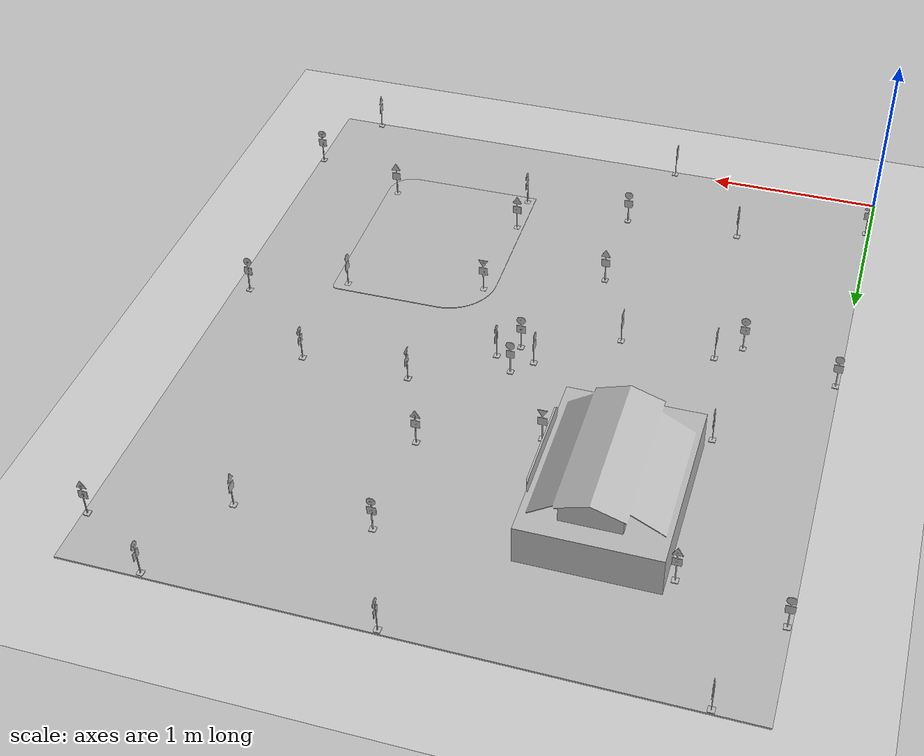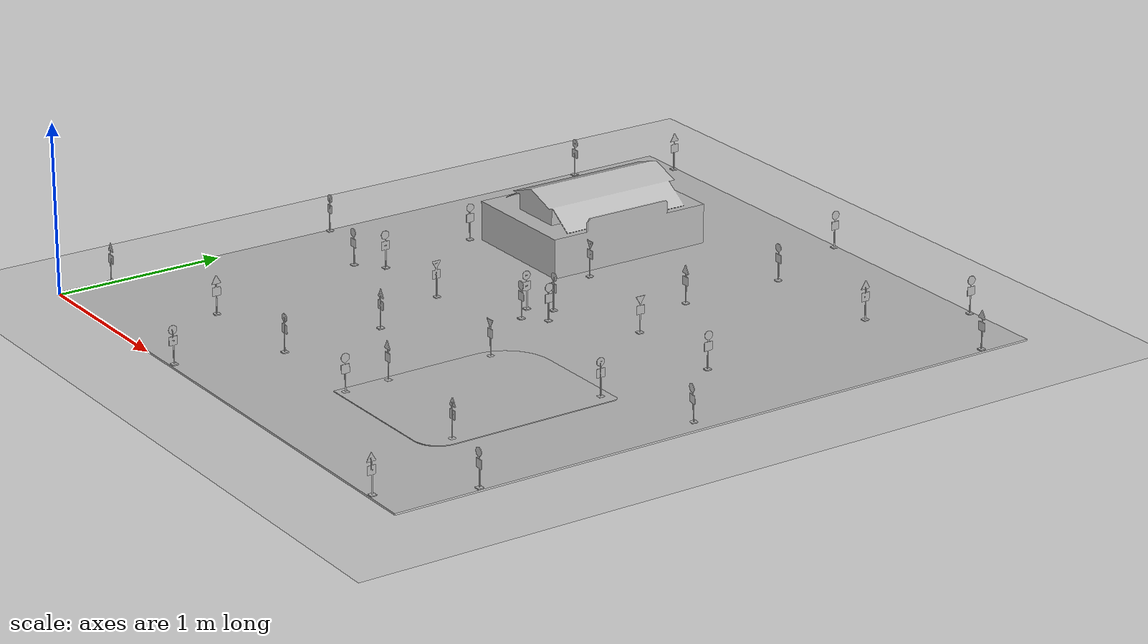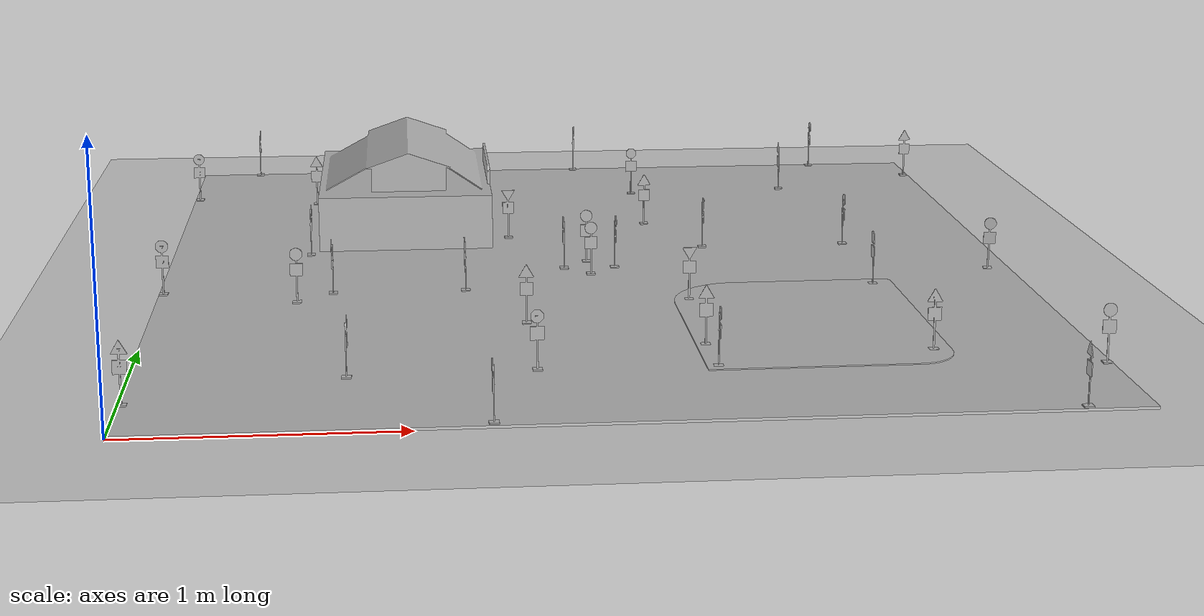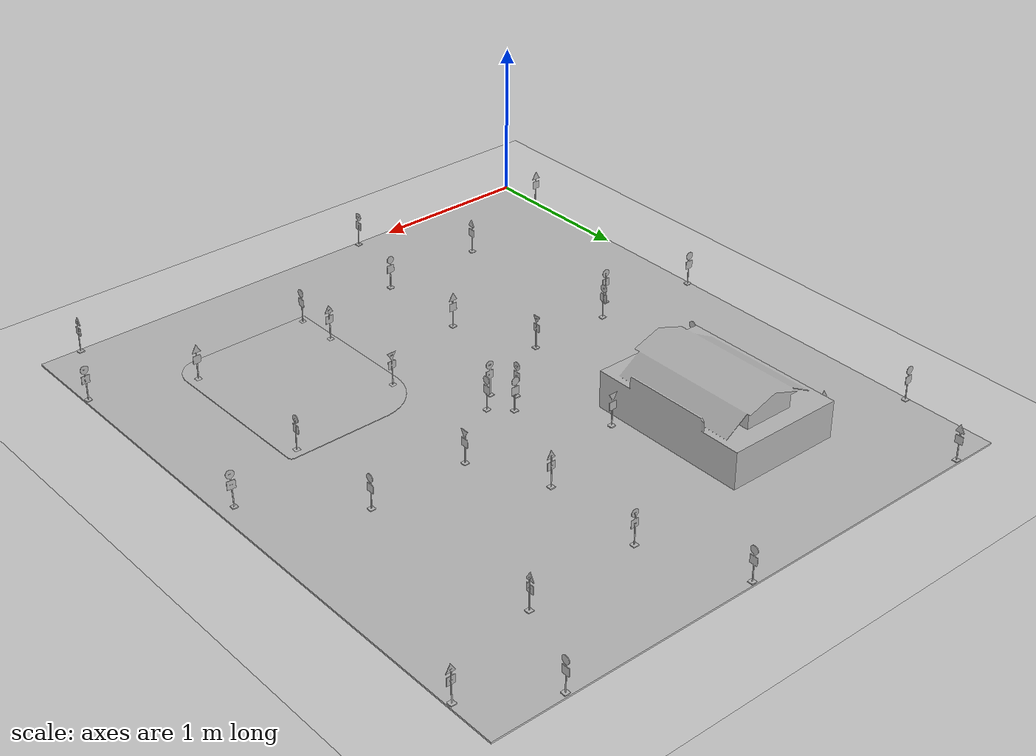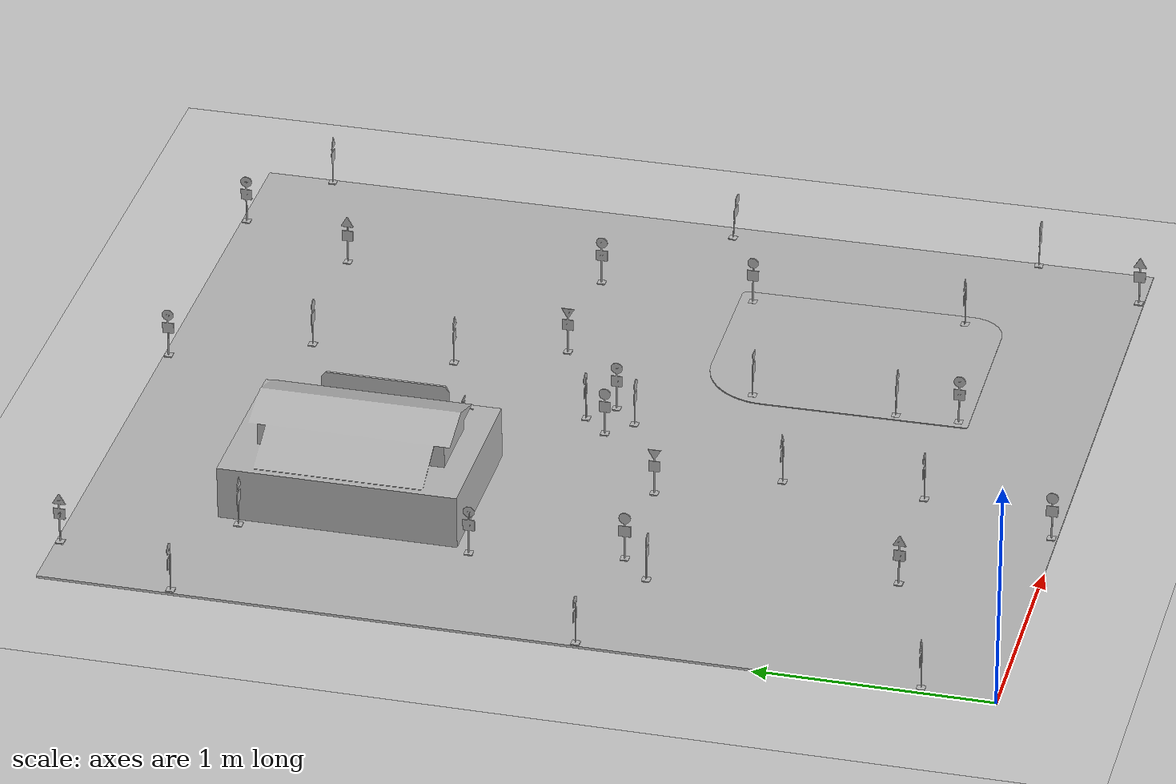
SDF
<sdf version="1.6">
 <world name="default">
  <light name="sun" type="directional">
   <pose>0 0 10 0 -0 0</pose>
   <diffuse>0.8 0.8 0.8 1</diffuse>
   <specular>0.1 0.1 0.1 1</specular>
   <attenuation>
    <range>1000</range>
    <constant>0.9</constant>
    <linear>0.01</linear>
    <quadratic>0.001</quadratic>
   </attenuation>
   <direction>-0.5 0.5 -1</direction>
  </light>
  <model name="ground_plane">
   <static>1</static>
   <link name="link">
    <collision name="collision">
     <geometry><plane><normal>0 0 1</normal><size>100 100</size></plane></geometry>
     <surface><friction><ode><mu>100</mu><mu2>50</mu2></ode></friction></surface>
    </collision>
    <visual name="visual">
     <cast_shadows>0</cast_shadows>
     <geometry><plane><normal>0 0 1</normal><size>100 100</size></plane></geometry>
     <material>
      <script><uri>file://media/materials/scripts/gazebo.material</uri><name>Gazebo/Grey</name></script>
     </material>
    </visual>
   </link>
  </model>
  <gravity>0 0 -9.8</gravity>
  <magnetic_field>6e-06 2.3e-05 -4.2e-05</magnetic_field>
  <atmosphere type="adiabatic"/>
  <physics name="default_physics" default="0" type="ode">
   <max_step_size>0.001</max_step_size>
   <real_time_factor>1</real_time_factor>
   <real_time_update_rate>1000</real_time_update_rate>
  </physics>
  <scene><ambient>0.4 0.4 0.4 1</ambient><background>0.7 0.7 0.7 1</background><shadows>1</shadows></scene>
  <spherical_coordinates>
   <surface_model>EARTH_WGS84</surface_model>
   <latitude_deg>0</latitude_deg>
   <longitude_deg>0</longitude_deg>
   <elevation>0</elevation>
   <heading_deg>0</heading_deg>
  </spherical_coordinates>
  <model name="bigcity">
   <pose>-0.000503 -0.002958 0.002788 0 -0 0</pose>
   <link name="link_0">
    <inertial>
     <mass>1</mass>
     <inertia>
      <ixx>0.166667</ixx>
      <ixy>0</ixy>
      <ixz>0</ixz>
      <iyy>0.166667</iyy>
      <iyz>0</iyz>
      <izz>0.166667</izz>
     </inertia>
    </inertial>
    <visual name="visual">
     <geometry><mesh><uri>file://models/stl/daeBlender/bigcity.dae</uri><scale>1 1 1</scale></mesh></geometry>
     <material><shader type="pixel"><normal_map>__default__</normal_map></shader></material>
    </visual>
    <collision name="collision">
     <pose>1.75 2 -0.03 0 -0 0</pose>
     <geometry><box><size>3.6 4.1 0.08</size></box></geometry>
     <surface>
      <friction>
       <ode><mu>1</mu><mu2>1</mu2><fdir1>0 0 0</fdir1><slip1>0</slip1><slip2>0</slip2></ode>
       <torsional>
        <coefficient>1</coefficient>
        <patch_radius>0</patch_radius>
        <surface_radius>0</surface_radius>
        <use_patch_radius>1</use_patch_radius>
        <ode><slip>0</slip></ode>
       </torsional>
      </friction>
      <bounce><restitution_coefficient>0</restitution_coefficient><threshold>1e+06</threshold></bounce>
      <contact>
       <collide_without_contact>0</collide_without_contact>
       <collide_without_contact_bitmask>1</collide_without_contact_bitmask>
       <collide_bitmask>1</collide_bitmask>
       <ode>
        <soft_cfm>0</soft_cfm>
        <soft_erp>0.2</soft_erp>
        <kp>1e+13</kp>
        <kd>1</kd>
        <max_vel>0.01</max_vel>
        <min_depth>0</min_depth>
       </ode>
       <bullet>
        <split_impulse>1</split_impulse>
        <split_impulse_penetration_threshold>-0.01</split_impulse_penetration_threshold>
        <soft_cfm>0</soft_cfm>
        <soft_erp>0.2</soft_erp>
        <kp>1e+13</kp>
        <kd>1</kd>
       </bullet>
      </contact>
     </surface>
    </collision>
   </link>
   <static>1</static>
  </model>
  <model name="rotonda_aruco">
   <link name="link_18">
    <inertial>
     <mass>0.02</mass>
     <inertia>
      <ixx>0.166667</ixx>
      <ixy>0</ixy>
      <ixz>0</ixz>
      <iyy>0.166667</iyy>
      <iyz>0</iyz>
      <izz>0.166667</izz>
     </inertia>
    </inertial>
    <visual name="visual">
     <geometry>
      <mesh><uri>file://models/stl/SENALES_ARUCOS/ROTONDA/rotonda_aruco.dae</uri><scale>1 1 1</scale></mesh>
     </geometry>
    </visual>
    <collision name="collision">
     <geometry>
      <mesh><uri>file://models/stl/SENALES_ARUCOS/ROTONDA/rotonda_aruco.dae</uri><scale>1 1 1</scale></mesh>
     </geometry>
     <surface>
      <friction>
       <ode><mu>1</mu><mu2>1</mu2><fdir1>0 0 0</fdir1><slip1>0</slip1><slip2>0</slip2></ode>
       <torsional>
        <coefficient>1</coefficient>
        <patch_radius>0</patch_radius>
        <surface_radius>0</surface_radius>
        <use_patch_radius>1</use_patch_radius>
        <ode><slip>0</slip></ode>
       </torsional>
      </friction>
      <bounce><restitution_coefficient>0</restitution_coefficient><threshold>1e+06</threshold></bounce>
      <contact>
       <collide_without_contact>0</collide_without_contact>
       <collide_without_contact_bitmask>1</collide_without_contact_bitmask>
       <collide_bitmask>1</collide_bitmask>
       <ode>
        <soft_cfm>0</soft_cfm>
        <soft_erp>0.2</soft_erp>
        <kp>1e+13</kp>
        <kd>1</kd>
        <max_vel>0.01</max_vel>
        <min_depth>0</min_depth>
       </ode>
       <bullet>
        <split_impulse>1</split_impulse>
        <split_impulse_penetration_threshold>-0.01</split_impulse_penetration_threshold>
        <soft_cfm>0</soft_cfm>
        <soft_erp>0.2</soft_erp>
        <kp>1e+13</kp>
        <kd>1</kd>
       </bullet>
      </contact>
     </surface>
    </collision>
   </link>
   <static>0</static>
   <pose>1.74663 1.90088 0.012778 0 -1e-06 0</pose>
  </model>
  <model name="parar_aruco">
   <link name="link_13">
    <inertial>
     <mass>0.02</mass>
     <inertia>
      <ixx>0.166667</ixx>
      <ixy>0</ixy>
      <ixz>0</ixz>
      <iyy>0.166667</iyy>
      <iyz>0</iyz>
      <izz>0.166667</izz>
     </inertia>
    </inertial>
    <visual name="visual">
     <geometry>
      <mesh><uri>file://models/stl/SENALES_ARUCOS/PARAR/parar_aruco.dae</uri><scale>1 1 1</scale></mesh>
     </geometry>
    </visual>
    <collision name="collision">
     <geometry>
      <mesh><uri>file://models/stl/SENALES_ARUCOS/PARAR/parar_aruco.dae</uri><scale>1 1 1</scale></mesh>
     </geometry>
     <surface>
      <friction>
       <ode><mu>1</mu><mu2>1</mu2><fdir1>0 0 0</fdir1><slip1>0</slip1><slip2>0</slip2></ode>
       <torsional>
        <coefficient>1</coefficient>
        <patch_radius>0</patch_radius>
        <surface_radius>0</surface_radius>
        <use_patch_radius>1</use_patch_radius>
        <ode><slip>0</slip></ode>
       </torsional>
      </friction>
      <bounce><restitution_coefficient>0</restitution_coefficient><threshold>1e+06</threshold></bounce>
      <contact>
       <collide_without_contact>0</collide_without_contact>
       <collide_without_contact_bitmask>1</collide_without_contact_bitmask>
       <collide_bitmask>1</collide_bitmask>
       <ode>
        <soft_cfm>0</soft_cfm>
        <soft_erp>0.2</soft_erp>
        <kp>1e+13</kp>
        <kd>1</kd>
        <max_vel>0.01</max_vel>
        <min_depth>0</min_depth>
       </ode>
       <bullet>
        <split_impulse>1</split_impulse>
        <split_impulse_penetration_threshold>-0.01</split_impulse_penetration_threshold>
        <soft_cfm>0</soft_cfm>
        <soft_erp>0.2</soft_erp>
        <kp>1e+13</kp>
        <kd>1</kd>
       </bullet>
      </contact>
     </surface>
    </collision>
   </link>
   <static>0</static>
   <pose>2.07435 3.39966 0.012778 3e-06 -0 0</pose>
  </model>
  <model name="peatones_aruco">
   <link name="link_15">
    <inertial>
     <mass>0.02</mass>
     <inertia>
      <ixx>0.166667</ixx>
      <ixy>0</ixy>
      <ixz>0</ixz>
      <iyy>0.166667</iyy>
      <iyz>0</iyz>
      <izz>0.166667</izz>
     </inertia>
    </inertial>
    <visual name="visual">
     <geometry>
      <mesh><uri>file://models/stl/SENALES_ARUCOS/PEATONES/peatones_aruco.dae</uri><scale>1 1 1</scale></mesh>
     </geometry>
    </visual>
    <collision name="collision">
     <geometry>
      <mesh><uri>file://models/stl/SENALES_ARUCOS/PEATONES/peatones_aruco.dae</uri><scale>1 1 1</scale></mesh>
     </geometry>
     <surface>
      <friction>
       <ode><mu>1</mu><mu2>1</mu2><fdir1>0 0 0</fdir1><slip1>0</slip1><slip2>0</slip2></ode>
       <torsional>
        <coefficient>1</coefficient>
        <patch_radius>0</patch_radius>
        <surface_radius>0</surface_radius>
        <use_patch_radius>1</use_patch_radius>
        <ode><slip>0</slip></ode>
       </torsional>
      </friction>
      <bounce><restitution_coefficient>0</restitution_coefficient><threshold>1e+06</threshold></bounce>
      <contact>
       <collide_without_contact>0</collide_without_contact>
       <collide_without_contact_bitmask>1</collide_without_contact_bitmask>
       <collide_bitmask>1</collide_bitmask>
       <ode>
        <soft_cfm>0</soft_cfm>
        <soft_erp>0.2</soft_erp>
        <kp>1e+13</kp>
        <kd>1</kd>
        <max_vel>0.01</max_vel>
        <min_depth>0</min_depth>
       </ode>
       <bullet>
        <split_impulse>1</split_impulse>
        <split_impulse_penetration_threshold>-0.01</split_impulse_penetration_threshold>
        <soft_cfm>0</soft_cfm>
        <soft_erp>0.2</soft_erp>
        <kp>1e+13</kp>
        <kd>1</kd>
       </bullet>
      </contact>
     </surface>
    </collision>
   </link>
   <static>0</static>
   <pose>2.07684 0.844264 0.012778 6e-06 1e-06 1.3e-05</pose>
  </model>
  <model name="ceda_aruco">
   <link name="link_9">
    <inertial>
     <mass>0.02</mass>
     <inertia>
      <ixx>0.166667</ixx>
      <ixy>0</ixy>
      <ixz>0</ixz>
      <iyy>0.166667</iyy>
      <iyz>0</iyz>
      <izz>0.166667</izz>
     </inertia>
    </inertial>
    <visual name="visual">
     <geometry>
      <mesh><uri>file://models/stl/SENALES_ARUCOS/CEDA/ceda_aruco.dae</uri><scale>1 1 1</scale></mesh>
     </geometry>
    </visual>
    <collision name="collision">
     <geometry>
      <mesh><uri>file://models/stl/SENALES_ARUCOS/CEDA/ceda_aruco.dae</uri><scale>1 1 1</scale></mesh>
     </geometry>
     <surface>
      <friction>
       <ode><mu>1</mu><mu2>1</mu2><fdir1>0 0 0</fdir1><slip1>0</slip1><slip2>0</slip2></ode>
       <torsional>
        <coefficient>1</coefficient>
        <patch_radius>0</patch_radius>
        <surface_radius>0</surface_radius>
        <use_patch_radius>1</use_patch_radius>
        <ode><slip>0</slip></ode>
       </torsional>
      </friction>
      <bounce><restitution_coefficient>0</restitution_coefficient><threshold>1e+06</threshold></bounce>
      <contact>
       <collide_without_contact>0</collide_without_contact>
       <collide_without_contact_bitmask>1</collide_without_contact_bitmask>
       <collide_bitmask>1</collide_bitmask>
       <ode>
        <soft_cfm>0</soft_cfm>
        <soft_erp>0.2</soft_erp>
        <kp>1e+13</kp>
        <kd>1</kd>
        <max_vel>0.01</max_vel>
        <min_depth>0</min_depth>
       </ode>
       <bullet>
        <split_impulse>1</split_impulse>
        <split_impulse_penetration_threshold>-0.01</split_impulse_penetration_threshold>
        <soft_cfm>0</soft_cfm>
        <soft_erp>0.2</soft_erp>
        <kp>1e+13</kp>
        <kd>1</kd>
       </bullet>
      </contact>
     </surface>
    </collision>
   </link>
   <static>0</static>
   <pose>2.0986 1.47002 0.012778 -3e-06 -7e-06 0</pose>
  </model>
  <model name="velocidad40_aruco">
   <link name="link_22">
    <inertial>
     <mass>0.02</mass>
     <inertia>
      <ixx>0.166667</ixx>
      <ixy>0</ixy>
      <ixz>0</ixz>
      <iyy>0.166667</iyy>
      <iyz>0</iyz>
      <izz>0.166667</izz>
     </inertia>
    </inertial>
    <visual name="visual">
     <geometry>
      <mesh><uri>file://models/stl/SENALES_ARUCOS/VELOCIDAD40/velo40_aruco.dae</uri><scale>1 1 1</scale></mesh>
     </geometry>
    </visual>
    <collision name="collision">
     <geometry>
      <mesh><uri>file://models/stl/SENALES_ARUCOS/VELOCIDAD40/velo40_aruco.dae</uri><scale>1 1 1</scale></mesh>
     </geometry>
     <surface>
      <friction>
       <ode><mu>1</mu><mu2>1</mu2><fdir1>0 0 0</fdir1><slip1>0</slip1><slip2>0</slip2></ode>
       <torsional>
        <coefficient>1</coefficient>
        <patch_radius>0</patch_radius>
        <surface_radius>0</surface_radius>
        <use_patch_radius>1</use_patch_radius>
        <ode><slip>0</slip></ode>
       </torsional>
      </friction>
      <bounce><restitution_coefficient>0</restitution_coefficient><threshold>1e+06</threshold></bounce>
      <contact>
       <collide_without_contact>0</collide_without_contact>
       <collide_without_contact_bitmask>1</collide_without_contact_bitmask>
       <collide_bitmask>1</collide_bitmask>
       <ode>
        <soft_cfm>0</soft_cfm>
        <soft_erp>0.2</soft_erp>
        <kp>1e+13</kp>
        <kd>1</kd>
        <max_vel>0.01</max_vel>
        <min_depth>0</min_depth>
       </ode>
       <bullet>
        <split_impulse>1</split_impulse>
        <split_impulse_penetration_threshold>-0.01</split_impulse_penetration_threshold>
        <soft_cfm>0</soft_cfm>
        <soft_erp>0.2</soft_erp>
        <kp>1e+13</kp>
        <kd>1</kd>
       </bullet>
      </contact>
     </surface>
    </collision>
   </link>
   <static>0</static>
   <pose>3.40801 1.85428 0.011068 0.064075 0.014868 -0.125364</pose>
  </model>
  <model name="rotonda_aruco_0">
   <link name="link_18">
    <inertial>
     <mass>0.02</mass>
     <inertia>
      <ixx>0.166667</ixx>
      <ixy>0</ixy>
      <ixz>0</ixz>
      <iyy>0.166667</iyy>
      <iyz>0</iyz>
      <izz>0.166667</izz>
     </inertia>
    </inertial>
    <visual name="visual">
     <geometry>
      <mesh><uri>file://models/stl/SENALES_ARUCOS/ROTONDA/rotonda_aruco.dae</uri><scale>1 1 1</scale></mesh>
     </geometry>
    </visual>
    <collision name="collision">
     <geometry>
      <mesh><uri>file://models/stl/SENALES_ARUCOS/ROTONDA/rotonda_aruco.dae</uri><scale>1 1 1</scale></mesh>
     </geometry>
     <surface>
      <friction>
       <ode><mu>1</mu><mu2>1</mu2><fdir1>0 0 0</fdir1><slip1>0</slip1><slip2>0</slip2></ode>
       <torsional>
        <coefficient>1</coefficient>
        <patch_radius>0</patch_radius>
        <surface_radius>0</surface_radius>
        <use_patch_radius>1</use_patch_radius>
        <ode><slip>0</slip></ode>
       </torsional>
      </friction>
      <bounce><restitution_coefficient>0</restitution_coefficient><threshold>1e+06</threshold></bounce>
      <contact>
       <collide_without_contact>0</collide_without_contact>
       <collide_without_contact_bitmask>1</collide_without_contact_bitmask>
       <collide_bitmask>1</collide_bitmask>
       <ode>
        <soft_cfm>0</soft_cfm>
        <soft_erp>0.2</soft_erp>
        <kp>1e+13</kp>
        <kd>1</kd>
        <max_vel>0.01</max_vel>
        <min_depth>0</min_depth>
       </ode>
       <bullet>
        <split_impulse>1</split_impulse>
        <split_impulse_penetration_threshold>-0.01</split_impulse_penetration_threshold>
        <soft_cfm>0</soft_cfm>
        <soft_erp>0.2</soft_erp>
        <kp>1e+13</kp>
        <kd>1</kd>
       </bullet>
      </contact>
     </surface>
    </collision>
   </link>
   <static>0</static>
   <pose>1.64213 2.00565 0.012788 4e-06 2e-06 -1.57655</pose>
  </model>
  <model name="rotonda_aruco_1">
   <link name="link_18">
    <inertial>
     <mass>0.02</mass>
     <inertia>
      <ixx>0.166667</ixx>
      <ixy>0</ixy>
      <ixz>0</ixz>
      <iyy>0.166667</iyy>
      <iyz>0</iyz>
      <izz>0.166667</izz>
     </inertia>
    </inertial>
    <visual name="visual">
     <geometry>
      <mesh><uri>file://models/stl/SENALES_ARUCOS/ROTONDA/rotonda_aruco.dae</uri><scale>1 1 1</scale></mesh>
     </geometry>
    </visual>
    <collision name="collision">
     <geometry>
      <mesh><uri>file://models/stl/SENALES_ARUCOS/ROTONDA/rotonda_aruco.dae</uri><scale>1 1 1</scale></mesh>
     </geometry>
     <surface>
      <friction>
       <ode><mu>1</mu><mu2>1</mu2><fdir1>0 0 0</fdir1><slip1>0</slip1><slip2>0</slip2></ode>
       <torsional>
        <coefficient>1</coefficient>
        <patch_radius>0</patch_radius>
        <surface_radius>0</surface_radius>
        <use_patch_radius>1</use_patch_radius>
        <ode><slip>0</slip></ode>
       </torsional>
      </friction>
      <bounce><restitution_coefficient>0</restitution_coefficient><threshold>1e+06</threshold></bounce>
      <contact>
       <collide_without_contact>0</collide_without_contact>
       <collide_without_contact_bitmask>1</collide_without_contact_bitmask>
       <collide_bitmask>1</collide_bitmask>
       <ode>
        <soft_cfm>0</soft_cfm>
        <soft_erp>0.2</soft_erp>
        <kp>1e+13</kp>
        <kd>1</kd>
        <max_vel>0.01</max_vel>
        <min_depth>0</min_depth>
       </ode>
       <bullet>
        <split_impulse>1</split_impulse>
        <split_impulse_penetration_threshold>-0.01</split_impulse_penetration_threshold>
        <soft_cfm>0</soft_cfm>
        <soft_erp>0.2</soft_erp>
        <kp>1e+13</kp>
        <kd>1</kd>
       </bullet>
      </contact>
     </surface>
    </collision>
   </link>
   <static>0</static>
   <pose>1.85758 2.00652 0.012778 -0 -1e-05 1.56964</pose>
  </model>
  <model name="rotonda_aruco_2">
   <link name="link_18">
    <inertial>
     <mass>0.02</mass>
     <inertia>
      <ixx>0.166667</ixx>
      <ixy>0</ixy>
      <ixz>0</ixz>
      <iyy>0.166667</iyy>
      <iyz>0</iyz>
      <izz>0.166667</izz>
     </inertia>
    </inertial>
    <visual name="visual">
     <geometry>
      <mesh><uri>file://models/stl/SENALES_ARUCOS/ROTONDA/rotonda_aruco.dae</uri><scale>1 1 1</scale></mesh>
     </geometry>
    </visual>
    <collision name="collision">
     <geometry>
      <mesh><uri>file://models/stl/SENALES_ARUCOS/ROTONDA/rotonda_aruco.dae</uri><scale>1 1 1</scale></mesh>
     </geometry>
     <surface>
      <friction>
       <ode><mu>1</mu><mu2>1</mu2><fdir1>0 0 0</fdir1><slip1>0</slip1><slip2>0</slip2></ode>
       <torsional>
        <coefficient>1</coefficient>
        <patch_radius>0</patch_radius>
        <surface_radius>0</surface_radius>
        <use_patch_radius>1</use_patch_radius>
        <ode><slip>0</slip></ode>
       </torsional>
      </friction>
      <bounce><restitution_coefficient>0</restitution_coefficient><threshold>1e+06</threshold></bounce>
      <contact>
       <collide_without_contact>0</collide_without_contact>
       <collide_without_contact_bitmask>1</collide_without_contact_bitmask>
       <collide_bitmask>1</collide_bitmask>
       <ode>
        <soft_cfm>0</soft_cfm>
        <soft_erp>0.2</soft_erp>
        <kp>1e+13</kp>
        <kd>1</kd>
        <max_vel>0.01</max_vel>
        <min_depth>0</min_depth>
       </ode>
       <bullet>
        <split_impulse>1</split_impulse>
        <split_impulse_penetration_threshold>-0.01</split_impulse_penetration_threshold>
        <soft_cfm>0</soft_cfm>
        <soft_erp>0.2</soft_erp>
        <kp>1e+13</kp>
        <kd>1</kd>
       </bullet>
      </contact>
     </surface>
    </collision>
   </link>
   <static>0</static>
   <pose>1.74617 2.11368 0.012778 9e-06 -1e-06 3.13013</pose>
  </model>
  <model name="peatones_aruco_0">
   <link name="link_15">
    <inertial>
     <mass>0.02</mass>
     <inertia>
      <ixx>0.166667</ixx>
      <ixy>0</ixy>
      <ixz>0</ixz>
      <iyy>0.166667</iyy>
      <iyz>0</iyz>
      <izz>0.166667</izz>
     </inertia>
    </inertial>
    <visual name="visual">
     <geometry>
      <mesh><uri>file://models/stl/SENALES_ARUCOS/PEATONES/peatones_aruco.dae</uri><scale>1 1 1</scale></mesh>
     </geometry>
    </visual>
    <collision name="collision">
     <geometry>
      <mesh><uri>file://models/stl/SENALES_ARUCOS/PEATONES/peatones_aruco.dae</uri><scale>1 1 1</scale></mesh>
     </geometry>
     <surface>
      <friction>
       <ode><mu>1</mu><mu2>1</mu2><fdir1>0 0 0</fdir1><slip1>0</slip1><slip2>0</slip2></ode>
       <torsional>
        <coefficient>1</coefficient>
        <patch_radius>0</patch_radius>
        <surface_radius>0</surface_radius>
        <use_patch_radius>1</use_patch_radius>
        <ode><slip>0</slip></ode>
       </torsional>
      </friction>
      <bounce><restitution_coefficient>0</restitution_coefficient><threshold>1e+06</threshold></bounce>
      <contact>
       <collide_without_contact>0</collide_without_contact>
       <collide_without_contact_bitmask>1</collide_without_contact_bitmask>
       <collide_bitmask>1</collide_bitmask>
       <ode>
        <soft_cfm>0</soft_cfm>
        <soft_erp>0.2</soft_erp>
        <kp>1e+13</kp>
        <kd>1</kd>
        <max_vel>0.01</max_vel>
        <min_depth>0</min_depth>
       </ode>
       <bullet>
        <split_impulse>1</split_impulse>
        <split_impulse_penetration_threshold>-0.01</split_impulse_penetration_threshold>
        <soft_cfm>0</soft_cfm>
        <soft_erp>0.2</soft_erp>
        <kp>1e+13</kp>
        <kd>1</kd>
       </bullet>
      </contact>
     </surface>
    </collision>
   </link>
   <static>0</static>
   <pose>2.06551 2.77134 0.012778 4e-06 3e-06 4e-05</pose>
  </model>
  <model name="peatones_aruco_1">
   <link name="link_15">
    <inertial>
     <mass>0.02</mass>
     <inertia>
      <ixx>0.166667</ixx>
      <ixy>0</ixy>
      <ixz>0</ixz>
      <iyy>0.166667</iyy>
      <iyz>0</iyz>
      <izz>0.166667</izz>
     </inertia>
    </inertial>
    <visual name="visual">
     <geometry>
      <mesh><uri>file://models/stl/SENALES_ARUCOS/PEATONES/peatones_aruco.dae</uri><scale>1 1 1</scale></mesh>
     </geometry>
    </visual>
    <collision name="collision">
     <geometry>
      <mesh><uri>file://models/stl/SENALES_ARUCOS/PEATONES/peatones_aruco.dae</uri><scale>1 1 1</scale></mesh>
     </geometry>
     <surface>
      <friction>
       <ode><mu>1</mu><mu2>1</mu2><fdir1>0 0 0</fdir1><slip1>0</slip1><slip2>0</slip2></ode>
       <torsional>
        <coefficient>1</coefficient>
        <patch_radius>0</patch_radius>
        <surface_radius>0</surface_radius>
        <use_patch_radius>1</use_patch_radius>
        <ode><slip>0</slip></ode>
       </torsional>
      </friction>
      <bounce><restitution_coefficient>0</restitution_coefficient><threshold>1e+06</threshold></bounce>
      <contact>
       <collide_without_contact>0</collide_without_contact>
       <collide_without_contact_bitmask>1</collide_without_contact_bitmask>
       <collide_bitmask>1</collide_bitmask>
       <ode>
        <soft_cfm>0</soft_cfm>
        <soft_erp>0.2</soft_erp>
        <kp>1e+13</kp>
        <kd>1</kd>
        <max_vel>0.01</max_vel>
        <min_depth>0</min_depth>
       </ode>
       <bullet>
        <split_impulse>1</split_impulse>
        <split_impulse_penetration_threshold>-0.01</split_impulse_penetration_threshold>
        <soft_cfm>0</soft_cfm>
        <soft_erp>0.2</soft_erp>
        <kp>1e+13</kp>
        <kd>1</kd>
       </bullet>
      </contact>
     </surface>
    </collision>
   </link>
   <static>0</static>
   <pose>1.43758 1.19522 0.012778 1e-06 -9e-06 3.11721</pose>
  </model>
  <model name="parar_aruco_0">
   <link name="link_13">
    <inertial>
     <mass>0.02</mass>
     <inertia>
      <ixx>0.166667</ixx>
      <ixy>0</ixy>
      <ixz>0</ixz>
      <iyy>0.166667</iyy>
      <iyz>0</iyz>
      <izz>0.166667</izz>
     </inertia>
    </inertial>
    <visual name="visual">
     <geometry>
      <mesh><uri>file://models/stl/SENALES_ARUCOS/PARAR/parar_aruco.dae</uri><scale>1 1 1</scale></mesh>
     </geometry>
    </visual>
    <collision name="collision">
     <geometry>
      <mesh><uri>file://models/stl/SENALES_ARUCOS/PARAR/parar_aruco.dae</uri><scale>1 1 1</scale></mesh>
     </geometry>
     <surface>
      <friction>
       <ode><mu>1</mu><mu2>1</mu2><fdir1>0 0 0</fdir1><slip1>0</slip1><slip2>0</slip2></ode>
       <torsional>
        <coefficient>1</coefficient>
        <patch_radius>0</patch_radius>
        <surface_radius>0</surface_radius>
        <use_patch_radius>1</use_patch_radius>
        <ode><slip>0</slip></ode>
       </torsional>
      </friction>
      <bounce><restitution_coefficient>0</restitution_coefficient><threshold>1e+06</threshold></bounce>
      <contact>
       <collide_without_contact>0</collide_without_contact>
       <collide_without_contact_bitmask>1</collide_without_contact_bitmask>
       <collide_bitmask>1</collide_bitmask>
       <ode>
        <soft_cfm>0</soft_cfm>
        <soft_erp>0.2</soft_erp>
        <kp>1e+13</kp>
        <kd>1</kd>
        <max_vel>0.01</max_vel>
        <min_depth>0</min_depth>
       </ode>
       <bullet>
        <split_impulse>1</split_impulse>
        <split_impulse_penetration_threshold>-0.01</split_impulse_penetration_threshold>
        <soft_cfm>0</soft_cfm>
        <soft_erp>0.2</soft_erp>
        <kp>1e+13</kp>
        <kd>1</kd>
       </bullet>
      </contact>
     </surface>
    </collision>
   </link>
   <static>0</static>
   <pose>0.585047 2.32253 0.012778 7e-06 1e-06 1.597</pose>
  </model>
  <model name="parar_aruco_1">
   <link name="link_13">
    <inertial>
     <mass>0.02</mass>
     <inertia>
      <ixx>0.166667</ixx>
      <ixy>0</ixy>
      <ixz>0</ixz>
      <iyy>0.166667</iyy>
      <iyz>0</iyz>
      <izz>0.166667</izz>
     </inertia>
    </inertial>
    <visual name="visual">
     <geometry>
      <mesh><uri>file://models/stl/SENALES_ARUCOS/PARAR/parar_aruco.dae</uri><scale>1 1 1</scale></mesh>
     </geometry>
    </visual>
    <collision name="collision">
     <geometry>
      <mesh><uri>file://models/stl/SENALES_ARUCOS/PARAR/parar_aruco.dae</uri><scale>1 1 1</scale></mesh>
     </geometry>
     <surface>
      <friction>
       <ode><mu>1</mu><mu2>1</mu2><fdir1>0 0 0</fdir1><slip1>0</slip1><slip2>0</slip2></ode>
       <torsional>
        <coefficient>1</coefficient>
        <patch_radius>0</patch_radius>
        <surface_radius>0</surface_radius>
        <use_patch_radius>1</use_patch_radius>
        <ode><slip>0</slip></ode>
       </torsional>
      </friction>
      <bounce><restitution_coefficient>0</restitution_coefficient><threshold>1e+06</threshold></bounce>
      <contact>
       <collide_without_contact>0</collide_without_contact>
       <collide_without_contact_bitmask>1</collide_without_contact_bitmask>
       <collide_bitmask>1</collide_bitmask>
       <ode>
        <soft_cfm>0</soft_cfm>
        <soft_erp>0.2</soft_erp>
        <kp>1e+13</kp>
        <kd>1</kd>
        <max_vel>0.01</max_vel>
        <min_depth>0</min_depth>
       </ode>
       <bullet>
        <split_impulse>1</split_impulse>
        <split_impulse_penetration_threshold>-0.01</split_impulse_penetration_threshold>
        <soft_cfm>0</soft_cfm>
        <soft_erp>0.2</soft_erp>
        <kp>1e+13</kp>
        <kd>1</kd>
       </bullet>
      </contact>
     </surface>
    </collision>
   </link>
   <static>0</static>
   <pose>2.87377 1.64574 0.012789 -5e-06 -2.4e-05 -1.58702</pose>
  </model>
  <model name="parar_aruco_2">
   <link name="link_13">
    <inertial>
     <mass>0.02</mass>
     <inertia>
      <ixx>0.166667</ixx>
      <ixy>0</ixy>
      <ixz>0</ixz>
      <iyy>0.166667</iyy>
      <iyz>0</iyz>
      <izz>0.166667</izz>
     </inertia>
    </inertial>
    <visual name="visual">
     <geometry>
      <mesh><uri>file://models/stl/SENALES_ARUCOS/PARAR/parar_aruco.dae</uri><scale>1 1 1</scale></mesh>
     </geometry>
    </visual>
    <collision name="collision">
     <geometry>
      <mesh><uri>file://models/stl/SENALES_ARUCOS/PARAR/parar_aruco.dae</uri><scale>1 1 1</scale></mesh>
     </geometry>
     <surface>
      <friction>
       <ode><mu>1</mu><mu2>1</mu2><fdir1>0 0 0</fdir1><slip1>0</slip1><slip2>0</slip2></ode>
       <torsional>
        <coefficient>1</coefficient>
        <patch_radius>0</patch_radius>
        <surface_radius>0</surface_radius>
        <use_patch_radius>1</use_patch_radius>
        <ode><slip>0</slip></ode>
       </torsional>
      </friction>
      <bounce><restitution_coefficient>0</restitution_coefficient><threshold>1e+06</threshold></bounce>
      <contact>
       <collide_without_contact>0</collide_without_contact>
       <collide_without_contact_bitmask>1</collide_without_contact_bitmask>
       <collide_bitmask>1</collide_bitmask>
       <ode>
        <soft_cfm>0</soft_cfm>
        <soft_erp>0.2</soft_erp>
        <kp>1e+13</kp>
        <kd>1</kd>
        <max_vel>0.01</max_vel>
        <min_depth>0</min_depth>
       </ode>
       <bullet>
        <split_impulse>1</split_impulse>
        <split_impulse_penetration_threshold>-0.01</split_impulse_penetration_threshold>
        <soft_cfm>0</soft_cfm>
        <soft_erp>0.2</soft_erp>
        <kp>1e+13</kp>
        <kd>1</kd>
       </bullet>
      </contact>
     </surface>
    </collision>
   </link>
   <static>0</static>
   <pose>1.43985 0.593023 0.012788 7e-06 -2e-06 3.13057</pose>
  </model>
  <model name="ceda_aruco_0">
   <link name="link_9">
    <inertial>
     <mass>0.02</mass>
     <inertia>
      <ixx>0.166667</ixx>
      <ixy>0</ixy>
      <ixz>0</ixz>
      <iyy>0.166667</iyy>
      <iyz>0</iyz>
      <izz>0.166667</izz>
     </inertia>
    </inertial>
    <visual name="visual">
     <geometry>
      <mesh><uri>file://models/stl/SENALES_ARUCOS/CEDA/ceda_aruco.dae</uri><scale>1 1 1</scale></mesh>
     </geometry>
    </visual>
    <collision name="collision">
     <geometry>
      <mesh><uri>file://models/stl/SENALES_ARUCOS/CEDA/ceda_aruco.dae</uri><scale>1 1 1</scale></mesh>
     </geometry>
     <surface>
      <friction>
       <ode><mu>1</mu><mu2>1</mu2><fdir1>0 0 0</fdir1><slip1>0</slip1><slip2>0</slip2></ode>
       <torsional>
        <coefficient>1</coefficient>
        <patch_radius>0</patch_radius>
        <surface_radius>0</surface_radius>
        <use_patch_radius>1</use_patch_radius>
        <ode><slip>0</slip></ode>
       </torsional>
      </friction>
      <bounce><restitution_coefficient>0</restitution_coefficient><threshold>1e+06</threshold></bounce>
      <contact>
       <collide_without_contact>0</collide_without_contact>
       <collide_without_contact_bitmask>1</collide_without_contact_bitmask>
       <collide_bitmask>1</collide_bitmask>
       <ode>
        <soft_cfm>0</soft_cfm>
        <soft_erp>0.2</soft_erp>
        <kp>1e+13</kp>
        <kd>1</kd>
        <max_vel>0.01</max_vel>
        <min_depth>0</min_depth>
       </ode>
       <bullet>
        <split_impulse>1</split_impulse>
        <split_impulse_penetration_threshold>-0.01</split_impulse_penetration_threshold>
        <soft_cfm>0</soft_cfm>
        <soft_erp>0.2</soft_erp>
        <kp>1e+13</kp>
        <kd>1</kd>
       </bullet>
      </contact>
     </surface>
    </collision>
   </link>
   <static>0</static>
   <pose>1.43993 2.56488 0.012786 2e-06 -1e-06 -3.14137</pose>
  </model>
  <model name="ceda_aruco_1">
   <link name="link_9">
    <inertial>
     <mass>0.02</mass>
     <inertia>
      <ixx>0.166667</ixx>
      <ixy>0</ixy>
      <ixz>0</ixz>
      <iyy>0.166667</iyy>
      <iyz>0</iyz>
      <izz>0.166667</izz>
     </inertia>
    </inertial>
    <visual name="visual">
     <geometry>
      <mesh><uri>file://models/stl/SENALES_ARUCOS/CEDA/ceda_aruco.dae</uri><scale>1 1 1</scale></mesh>
     </geometry>
    </visual>
    <collision name="collision">
     <geometry>
      <mesh><uri>file://models/stl/SENALES_ARUCOS/CEDA/ceda_aruco.dae</uri><scale>1 1 1</scale></mesh>
     </geometry>
     <surface>
      <friction>
       <ode><mu>1</mu><mu2>1</mu2><fdir1>0 0 0</fdir1><slip1>0</slip1><slip2>0</slip2></ode>
       <torsional>
        <coefficient>1</coefficient>
        <patch_radius>0</patch_radius>
        <surface_radius>0</surface_radius>
        <use_patch_radius>1</use_patch_radius>
        <ode><slip>0</slip></ode>
       </torsional>
      </friction>
      <bounce><restitution_coefficient>0</restitution_coefficient><threshold>1e+06</threshold></bounce>
      <contact>
       <collide_without_contact>0</collide_without_contact>
       <collide_without_contact_bitmask>1</collide_without_contact_bitmask>
       <collide_bitmask>1</collide_bitmask>
       <ode>
        <soft_cfm>0</soft_cfm>
        <soft_erp>0.2</soft_erp>
        <kp>1e+13</kp>
        <kd>1</kd>
        <max_vel>0.01</max_vel>
        <min_depth>0</min_depth>
       </ode>
       <bullet>
        <split_impulse>1</split_impulse>
        <split_impulse_penetration_threshold>-0.01</split_impulse_penetration_threshold>
        <soft_cfm>0</soft_cfm>
        <soft_erp>0.2</soft_erp>
        <kp>1e+13</kp>
        <kd>1</kd>
       </bullet>
      </contact>
     </surface>
    </collision>
   </link>
   <static>0</static>
   <pose>1.22076 1.69149 0.012788 1e-06 -7e-06 -1.56926</pose>
  </model>
  <model name="ceda_aruco_2">
   <link name="link_9">
    <inertial>
     <mass>0.02</mass>
     <inertia>
      <ixx>0.166667</ixx>
      <ixy>0</ixy>
      <ixz>0</ixz>
      <iyy>0.166667</iyy>
      <iyz>0</iyz>
      <izz>0.166667</izz>
     </inertia>
    </inertial>
    <visual name="visual">
     <geometry>
      <mesh><uri>file://models/stl/SENALES_ARUCOS/CEDA/ceda_aruco.dae</uri><scale>1 1 1</scale></mesh>
     </geometry>
    </visual>
    <collision name="collision">
     <geometry>
      <mesh><uri>file://models/stl/SENALES_ARUCOS/CEDA/ceda_aruco.dae</uri><scale>1 1 1</scale></mesh>
     </geometry>
     <surface>
      <friction>
       <ode><mu>1</mu><mu2>1</mu2><fdir1>0 0 0</fdir1><slip1>0</slip1><slip2>0</slip2></ode>
       <torsional>
        <coefficient>1</coefficient>
        <patch_radius>0</patch_radius>
        <surface_radius>0</surface_radius>
        <use_patch_radius>1</use_patch_radius>
        <ode><slip>0</slip></ode>
       </torsional>
      </friction>
      <bounce><restitution_coefficient>0</restitution_coefficient><threshold>1e+06</threshold></bounce>
      <contact>
       <collide_without_contact>0</collide_without_contact>
       <collide_without_contact_bitmask>1</collide_without_contact_bitmask>
       <collide_bitmask>1</collide_bitmask>
       <ode>
        <soft_cfm>0</soft_cfm>
        <soft_erp>0.2</soft_erp>
        <kp>1e+13</kp>
        <kd>1</kd>
        <max_vel>0.01</max_vel>
        <min_depth>0</min_depth>
       </ode>
       <bullet>
        <split_impulse>1</split_impulse>
        <split_impulse_penetration_threshold>-0.01</split_impulse_penetration_threshold>
        <soft_cfm>0</soft_cfm>
        <soft_erp>0.2</soft_erp>
        <kp>1e+13</kp>
        <kd>1</kd>
       </bullet>
      </contact>
     </surface>
    </collision>
   </link>
   <static>0</static>
   <pose>2.27054 2.32105 0.012779 0 -1.4e-05 1.54448</pose>
  </model>
  <model name="peligro_izqu_aruco">
   <link name="link_17">
    <inertial>
     <mass>0.02</mass>
     <inertia>
      <ixx>0.166667</ixx>
      <ixy>0</ixy>
      <ixz>0</ixz>
      <iyy>0.166667</iyy>
      <iyz>0</iyz>
      <izz>0.166667</izz>
     </inertia>
    </inertial>
    <visual name="visual">
     <geometry>
      <mesh><uri>model://stl/SENALES_ARUCOS/PELIGRO IZQUIERDA/peligr_izq_aruco.dae</uri><scale>1 1 1</scale></mesh>
     </geometry>
    </visual>
    <collision name="collision">
     <geometry>
      <mesh>
       <uri>file://models/stl/SENALES_ARUCOS/PELIGRO IZQUIERDA/peligr_izq_aruco.dae</uri>
       <scale>1 1 1</scale>
      </mesh>
     </geometry>
     <surface>
      <friction>
       <ode><mu>1</mu><mu2>1</mu2><fdir1>0 0 0</fdir1><slip1>0</slip1><slip2>0</slip2></ode>
       <torsional>
        <coefficient>1</coefficient>
        <patch_radius>0</patch_radius>
        <surface_radius>0</surface_radius>
        <use_patch_radius>1</use_patch_radius>
        <ode><slip>0</slip></ode>
       </torsional>
      </friction>
      <bounce><restitution_coefficient>0</restitution_coefficient><threshold>1e+06</threshold></bounce>
      <contact>
       <collide_without_contact>0</collide_without_contact>
       <collide_without_contact_bitmask>1</collide_without_contact_bitmask>
       <collide_bitmask>1</collide_bitmask>
       <ode>
        <soft_cfm>0</soft_cfm>
        <soft_erp>0.2</soft_erp>
        <kp>1e+13</kp>
        <kd>1</kd>
        <max_vel>0.01</max_vel>
        <min_depth>0</min_depth>
       </ode>
       <bullet>
        <split_impulse>1</split_impulse>
        <split_impulse_penetration_threshold>-0.01</split_impulse_penetration_threshold>
        <soft_cfm>0</soft_cfm>
        <soft_erp>0.2</soft_erp>
        <kp>1e+13</kp>
        <kd>1</kd>
       </bullet>
      </contact>
     </surface>
    </collision>
   </link>
   <static>0</static>
   <pose>2.89878 0.715564 0.012778 5e-06 -2e-06 -3.12946</pose>
  </model>
  <model name="peligro_izqu_aruco_0">
   <link name="link_17">
    <inertial>
     <mass>0.02</mass>
     <inertia>
      <ixx>0.166667</ixx>
      <ixy>0</ixy>
      <ixz>0</ixz>
      <iyy>0.166667</iyy>
      <iyz>0</iyz>
      <izz>0.166667</izz>
     </inertia>
    </inertial>
    <visual name="visual">
     <geometry>
      <mesh>
       <uri>file://models/stl/SENALES_ARUCOS/PELIGRO IZQUIERDA/peligr_izq_aruco.dae</uri>
       <scale>1 1 1</scale>
      </mesh>
     </geometry>
    </visual>
    <collision name="collision">
     <geometry>
      <mesh>
       <uri>file://models/stl/SENALES_ARUCOS/PELIGRO IZQUIERDA/peligr_izq_aruco.dae</uri>
       <scale>1 1 1</scale>
      </mesh>
     </geometry>
     <surface>
      <friction>
       <ode><mu>1</mu><mu2>1</mu2><fdir1>0 0 0</fdir1><slip1>0</slip1><slip2>0</slip2></ode>
       <torsional>
        <coefficient>1</coefficient>
        <patch_radius>0</patch_radius>
        <surface_radius>0</surface_radius>
        <use_patch_radius>1</use_patch_radius>
        <ode><slip>0</slip></ode>
       </torsional>
      </friction>
      <bounce><restitution_coefficient>0</restitution_coefficient><threshold>1e+06</threshold></bounce>
      <contact>
       <collide_without_contact>0</collide_without_contact>
       <collide_without_contact_bitmask>1</collide_without_contact_bitmask>
       <collide_bitmask>1</collide_bitmask>
       <ode>
        <soft_cfm>0</soft_cfm>
        <soft_erp>0.2</soft_erp>
        <kp>1e+13</kp>
        <kd>1</kd>
        <max_vel>0.01</max_vel>
        <min_depth>0</min_depth>
       </ode>
       <bullet>
        <split_impulse>1</split_impulse>
        <split_impulse_penetration_threshold>-0.01</split_impulse_penetration_threshold>
        <soft_cfm>0</soft_cfm>
        <soft_erp>0.2</soft_erp>
        <kp>1e+13</kp>
        <kd>1</kd>
       </bullet>
      </contact>
     </surface>
    </collision>
   </link>
   <static>0</static>
   <pose>0.768576 0.55965 0.012779 5e-06 -8e-06 1.51209</pose>
  </model>
  <model name="peligro_izqu_aruco_1">
   <link name="link_17">
    <inertial>
     <mass>0.02</mass>
     <inertia>
      <ixx>0.166667</ixx>
      <ixy>0</ixy>
      <ixz>0</ixz>
      <iyy>0.166667</iyy>
      <iyz>0</iyz>
      <izz>0.166667</izz>
     </inertia>
    </inertial>
    <visual name="visual">
     <geometry>
      <mesh>
       <uri>file://models/stl/SENALES_ARUCOS/PELIGRO IZQUIERDA/peligr_izq_aruco.dae</uri>
       <scale>1 1 1</scale>
      </mesh>
     </geometry>
    </visual>
    <collision name="collision">
     <geometry>
      <mesh>
       <uri>file://models/stl/SENALES_ARUCOS/PELIGRO IZQUIERDA/peligr_izq_aruco.dae</uri>
       <scale>1 1 1</scale>
      </mesh>
     </geometry>
     <surface>
      <friction>
       <ode><mu>1</mu><mu2>1</mu2><fdir1>0 0 0</fdir1><slip1>0</slip1><slip2>0</slip2></ode>
       <torsional>
        <coefficient>1</coefficient>
        <patch_radius>0</patch_radius>
        <surface_radius>0</surface_radius>
        <use_patch_radius>1</use_patch_radius>
        <ode><slip>0</slip></ode>
       </torsional>
      </friction>
      <bounce><restitution_coefficient>0</restitution_coefficient><threshold>1e+06</threshold></bounce>
      <contact>
       <collide_without_contact>0</collide_without_contact>
       <collide_without_contact_bitmask>1</collide_without_contact_bitmask>
       <collide_bitmask>1</collide_bitmask>
       <ode>
        <soft_cfm>0</soft_cfm>
        <soft_erp>0.2</soft_erp>
        <kp>1e+13</kp>
        <kd>1</kd>
        <max_vel>0.01</max_vel>
        <min_depth>0</min_depth>
       </ode>
       <bullet>
        <split_impulse>1</split_impulse>
        <split_impulse_penetration_threshold>-0.01</split_impulse_penetration_threshold>
        <soft_cfm>0</soft_cfm>
        <soft_erp>0.2</soft_erp>
        <kp>1e+13</kp>
        <kd>1</kd>
       </bullet>
      </contact>
     </surface>
    </collision>
   </link>
   <static>0</static>
   <pose>2.79864 3.44332 0.012779 -8e-06 -1e-06 -1.58779</pose>
  </model>
  <model name="peligro_izqu_aruco_2">
   <link name="link_17">
    <inertial>
     <mass>0.02</mass>
     <inertia>
      <ixx>0.166667</ixx>
      <ixy>0</ixy>
      <ixz>0</ixz>
      <iyy>0.166667</iyy>
      <iyz>0</iyz>
      <izz>0.166667</izz>
     </inertia>
    </inertial>
    <visual name="visual">
     <geometry>
      <mesh>
       <uri>file://models/stl/SENALES_ARUCOS/PELIGRO IZQUIERDA/peligr_izq_aruco.dae</uri>
       <scale>1 1 1</scale>
      </mesh>
     </geometry>
    </visual>
    <collision name="collision">
     <geometry>
      <mesh>
       <uri>file://models/stl/SENALES_ARUCOS/PELIGRO IZQUIERDA/peligr_izq_aruco.dae</uri>
       <scale>1 1 1</scale>
      </mesh>
     </geometry>
     <surface>
      <friction>
       <ode><mu>1</mu><mu2>1</mu2><fdir1>0 0 0</fdir1><slip1>0</slip1><slip2>0</slip2></ode>
       <torsional>
        <coefficient>1</coefficient>
        <patch_radius>0</patch_radius>
        <surface_radius>0</surface_radius>
        <use_patch_radius>1</use_patch_radius>
        <ode><slip>0</slip></ode>
       </torsional>
      </friction>
      <bounce><restitution_coefficient>0</restitution_coefficient><threshold>1e+06</threshold></bounce>
      <contact>
       <collide_without_contact>0</collide_without_contact>
       <collide_without_contact_bitmask>1</collide_without_contact_bitmask>
       <collide_bitmask>1</collide_bitmask>
       <ode>
        <soft_cfm>0</soft_cfm>
        <soft_erp>0.2</soft_erp>
        <kp>1e+13</kp>
        <kd>1</kd>
        <max_vel>0.01</max_vel>
        <min_depth>0</min_depth>
       </ode>
       <bullet>
        <split_impulse>1</split_impulse>
        <split_impulse_penetration_threshold>-0.01</split_impulse_penetration_threshold>
        <soft_cfm>0</soft_cfm>
        <soft_erp>0.2</soft_erp>
        <kp>1e+13</kp>
        <kd>1</kd>
       </bullet>
      </contact>
     </surface>
    </collision>
   </link>
   <static>0</static>
   <pose>0.577549 3.30121 0.012778 5e-06 3e-06 -1e-06</pose>
  </model>
  <model name="velocidad50_aruco">
   <link name="link_23">
    <inertial>
     <mass>0.02</mass>
     <inertia>
      <ixx>0.166667</ixx>
      <ixy>0</ixy>
      <ixz>0</ixz>
      <iyy>0.166667</iyy>
      <iyz>0</iyz>
      <izz>0.166667</izz>
     </inertia>
    </inertial>
    <visual name="visual">
     <geometry>
      <mesh><uri>file://models/stl/SENALES_ARUCOS/VELOCIDAD50/velo50_aruco.dae</uri><scale>1 1 1</scale></mesh>
     </geometry>
    </visual>
    <collision name="collision">
     <geometry>
      <mesh><uri>file://models/stl/SENALES_ARUCOS/VELOCIDAD50/velo50_aruco.dae</uri><scale>1 1 1</scale></mesh>
     </geometry>
     <surface>
      <friction>
       <ode><mu>1</mu><mu2>1</mu2><fdir1>0 0 0</fdir1><slip1>0</slip1><slip2>0</slip2></ode>
       <torsional>
        <coefficient>1</coefficient>
        <patch_radius>0</patch_radius>
        <surface_radius>0</surface_radius>
        <use_patch_radius>1</use_patch_radius>
        <ode><slip>0</slip></ode>
       </torsional>
      </friction>
      <bounce><restitution_coefficient>0</restitution_coefficient><threshold>1e+06</threshold></bounce>
      <contact>
       <collide_without_contact>0</collide_without_contact>
       <collide_without_contact_bitmask>1</collide_without_contact_bitmask>
       <collide_bitmask>1</collide_bitmask>
       <ode>
        <soft_cfm>0</soft_cfm>
        <soft_erp>0.2</soft_erp>
        <kp>1e+13</kp>
        <kd>1</kd>
        <max_vel>0.01</max_vel>
        <min_depth>0</min_depth>
       </ode>
       <bullet>
        <split_impulse>1</split_impulse>
        <split_impulse_penetration_threshold>-0.01</split_impulse_penetration_threshold>
        <soft_cfm>0</soft_cfm>
        <soft_erp>0.2</soft_erp>
        <kp>1e+13</kp>
        <kd>1</kd>
       </bullet>
      </contact>
     </surface>
    </collision>
   </link>
   <static>0</static>
   <pose>0.021042 3.43181 0.012778 7e-06 -6e-06 -3.12205</pose>
  </model>
  <model name="peligro_dcha_aruco">
   <link name="link_16">
    <inertial>
     <mass>0.02</mass>
     <inertia>
      <ixx>0.166667</ixx>
      <ixy>0</ixy>
      <ixz>0</ixz>
      <iyy>0.166667</iyy>
      <iyz>0</iyz>
      <izz>0.166667</izz>
     </inertia>
    </inertial>
    <visual name="visual">
     <geometry>
      <mesh>
       <uri>file://models/stl/SENALES_ARUCOS/PELIGRO DERECHA/peligr_dcha_aruco.dae</uri>
       <scale>1 1 1</scale>
      </mesh>
     </geometry>
    </visual>
    <collision name="collision">
     <geometry>
      <mesh>
       <uri>file://models/stl/SENALES_ARUCOS/PELIGRO DERECHA/peligr_dcha_aruco.dae</uri>
       <scale>1 1 1</scale>
      </mesh>
     </geometry>
     <surface>
      <friction>
       <ode><mu>1</mu><mu2>1</mu2><fdir1>0 0 0</fdir1><slip1>0</slip1><slip2>0</slip2></ode>
       <torsional>
        <coefficient>1</coefficient>
        <patch_radius>0</patch_radius>
        <surface_radius>0</surface_radius>
        <use_patch_radius>1</use_patch_radius>
        <ode><slip>0</slip></ode>
       </torsional>
      </friction>
      <bounce><restitution_coefficient>0</restitution_coefficient><threshold>1e+06</threshold></bounce>
      <contact>
       <collide_without_contact>0</collide_without_contact>
       <collide_without_contact_bitmask>1</collide_without_contact_bitmask>
       <collide_bitmask>1</collide_bitmask>
       <ode>
        <soft_cfm>0</soft_cfm>
        <soft_erp>0.2</soft_erp>
        <kp>1e+13</kp>
        <kd>1</kd>
        <max_vel>0.01</max_vel>
        <min_depth>0</min_depth>
       </ode>
       <bullet>
        <split_impulse>1</split_impulse>
        <split_impulse_penetration_threshold>-0.01</split_impulse_penetration_threshold>
        <soft_cfm>0</soft_cfm>
        <soft_erp>0.2</soft_erp>
        <kp>1e+13</kp>
        <kd>1</kd>
       </bullet>
      </contact>
     </surface>
    </collision>
   </link>
   <static>0</static>
   <pose>0.275306 3.9775 0.012788 2e-06 -4e-06 1.57611</pose>
  </model>
  <model name="peligro_dcha_aruco_0">
   <link name="link_16">
    <inertial>
     <mass>0.02</mass>
     <inertia>
      <ixx>0.166667</ixx>
      <ixy>0</ixy>
      <ixz>0</ixz>
      <iyy>0.166667</iyy>
      <iyz>0</iyz>
      <izz>0.166667</izz>
     </inertia>
    </inertial>
    <visual name="visual">
     <geometry>
      <mesh>
       <uri>file://models/stl/SENALES_ARUCOS/PELIGRO DERECHA/peligr_dcha_aruco.dae</uri>
       <scale>1 1 1</scale>
      </mesh>
     </geometry>
    </visual>
    <collision name="collision">
     <geometry>
      <mesh>
       <uri>file://models/stl/SENALES_ARUCOS/PELIGRO DERECHA/peligr_dcha_aruco.dae</uri>
       <scale>1 1 1</scale>
      </mesh>
     </geometry>
     <surface>
      <friction>
       <ode><mu>1</mu><mu2>1</mu2><fdir1>0 0 0</fdir1><slip1>0</slip1><slip2>0</slip2></ode>
       <torsional>
        <coefficient>1</coefficient>
        <patch_radius>0</patch_radius>
        <surface_radius>0</surface_radius>
        <use_patch_radius>1</use_patch_radius>
        <ode><slip>0</slip></ode>
       </torsional>
      </friction>
      <bounce><restitution_coefficient>0</restitution_coefficient><threshold>1e+06</threshold></bounce>
      <contact>
       <collide_without_contact>0</collide_without_contact>
       <collide_without_contact_bitmask>1</collide_without_contact_bitmask>
       <collide_bitmask>1</collide_bitmask>
       <ode>
        <soft_cfm>0</soft_cfm>
        <soft_erp>0.2</soft_erp>
        <kp>1e+13</kp>
        <kd>1</kd>
        <max_vel>0.01</max_vel>
        <min_depth>0</min_depth>
       </ode>
       <bullet>
        <split_impulse>1</split_impulse>
        <split_impulse_penetration_threshold>-0.01</split_impulse_penetration_threshold>
        <soft_cfm>0</soft_cfm>
        <soft_erp>0.2</soft_erp>
        <kp>1e+13</kp>
        <kd>1</kd>
       </bullet>
      </contact>
     </surface>
    </collision>
   </link>
   <static>0</static>
   <pose>0.018689 0.313069 0.012788 7e-06 -1e-06 3.13759</pose>
  </model>
  <model name="peligro_dcha_aruco_1">
   <link name="link_16">
    <inertial>
     <mass>0.02</mass>
     <inertia>
      <ixx>0.166667</ixx>
      <ixy>0</ixy>
      <ixz>0</ixz>
      <iyy>0.166667</iyy>
      <iyz>0</iyz>
      <izz>0.166667</izz>
     </inertia>
    </inertial>
    <visual name="visual">
     <geometry>
      <mesh>
       <uri>file://models/stl/SENALES_ARUCOS/PELIGRO DERECHA/peligr_dcha_aruco.dae</uri>
       <scale>1 1 1</scale>
      </mesh>
     </geometry>
    </visual>
    <collision name="collision">
     <geometry>
      <mesh>
       <uri>file://models/stl/SENALES_ARUCOS/PELIGRO DERECHA/peligr_dcha_aruco.dae</uri>
       <scale>1 1 1</scale>
      </mesh>
     </geometry>
     <surface>
      <friction>
       <ode><mu>1</mu><mu2>1</mu2><fdir1>0 0 0</fdir1><slip1>0</slip1><slip2>0</slip2></ode>
       <torsional>
        <coefficient>1</coefficient>
        <patch_radius>0</patch_radius>
        <surface_radius>0</surface_radius>
        <use_patch_radius>1</use_patch_radius>
        <ode><slip>0</slip></ode>
       </torsional>
      </friction>
      <bounce><restitution_coefficient>0</restitution_coefficient><threshold>1e+06</threshold></bounce>
      <contact>
       <collide_without_contact>0</collide_without_contact>
       <collide_without_contact_bitmask>1</collide_without_contact_bitmask>
       <collide_bitmask>1</collide_bitmask>
       <ode>
        <soft_cfm>0</soft_cfm>
        <soft_erp>0.2</soft_erp>
        <kp>1e+13</kp>
        <kd>1</kd>
        <max_vel>0.01</max_vel>
        <min_depth>0</min_depth>
       </ode>
       <bullet>
        <split_impulse>1</split_impulse>
        <split_impulse_penetration_threshold>-0.01</split_impulse_penetration_threshold>
        <soft_cfm>0</soft_cfm>
        <soft_erp>0.2</soft_erp>
        <kp>1e+13</kp>
        <kd>1</kd>
       </bullet>
      </contact>
     </surface>
    </collision>
   </link>
   <static>0</static>
   <pose>3.25517 0.018067 0.012778 4e-06 1e-06 -1.56493</pose>
  </model>
  <model name="peligro_dcha_aruco_2">
   <link name="link_16">
    <inertial>
     <mass>0.02</mass>
     <inertia>
      <ixx>0.166667</ixx>
      <ixy>0</ixy>
      <ixz>0</ixz>
      <iyy>0.166667</iyy>
      <iyz>0</iyz>
      <izz>0.166667</izz>
     </inertia>
    </inertial>
    <visual name="visual">
     <geometry>
      <mesh>
       <uri>file://models/stl/SENALES_ARUCOS/PELIGRO DERECHA/peligr_dcha_aruco.dae</uri>
       <scale>1 1 1</scale>
      </mesh>
     </geometry>
    </visual>
    <collision name="collision">
     <geometry>
      <mesh>
       <uri>file://models/stl/SENALES_ARUCOS/PELIGRO DERECHA/peligr_dcha_aruco.dae</uri>
       <scale>1 1 1</scale>
      </mesh>
     </geometry>
     <surface>
      <friction>
       <ode><mu>1</mu><mu2>1</mu2><fdir1>0 0 0</fdir1><slip1>0</slip1><slip2>0</slip2></ode>
       <torsional>
        <coefficient>1</coefficient>
        <patch_radius>0</patch_radius>
        <surface_radius>0</surface_radius>
        <use_patch_radius>1</use_patch_radius>
        <ode><slip>0</slip></ode>
       </torsional>
      </friction>
      <bounce><restitution_coefficient>0</restitution_coefficient><threshold>1e+06</threshold></bounce>
      <contact>
       <collide_without_contact>0</collide_without_contact>
       <collide_without_contact_bitmask>1</collide_without_contact_bitmask>
       <collide_bitmask>1</collide_bitmask>
       <ode>
        <soft_cfm>0</soft_cfm>
        <soft_erp>0.2</soft_erp>
        <kp>1e+13</kp>
        <kd>1</kd>
        <max_vel>0.01</max_vel>
        <min_depth>0</min_depth>
       </ode>
       <bullet>
        <split_impulse>1</split_impulse>
        <split_impulse_penetration_threshold>-0.01</split_impulse_penetration_threshold>
        <soft_cfm>0</soft_cfm>
        <soft_erp>0.2</soft_erp>
        <kp>1e+13</kp>
        <kd>1</kd>
       </bullet>
      </contact>
     </surface>
    </collision>
   </link>
   <static>0</static>
   <pose>3.47668 3.69682 0.012778 2e-06 -5e-06 6e-06</pose>
  </model>
  <model name="velocidad20_aruco_0">
   <link name="link_21">
    <inertial>
     <mass>0.02</mass>
     <inertia>
      <ixx>0.166667</ixx>
      <ixy>0</ixy>
      <ixz>0</ixz>
      <iyy>0.166667</iyy>
      <iyz>0</iyz>
      <izz>0.166667</izz>
     </inertia>
    </inertial>
    <visual name="visual">
     <geometry>
      <mesh><uri>file://models/stl/SENALES_ARUCOS/VELOCIDAD20/velo20_aruco.dae</uri><scale>1 1 1</scale></mesh>
     </geometry>
    </visual>
    <collision name="collision">
     <geometry>
      <mesh><uri>file://models/stl/SENALES_ARUCOS/VELOCIDAD20/velo20_aruco.dae</uri><scale>1 1 1</scale></mesh>
     </geometry>
     <surface>
      <friction>
       <ode><mu>1</mu><mu2>1</mu2><fdir1>0 0 0</fdir1><slip1>0</slip1><slip2>0</slip2></ode>
       <torsional>
        <coefficient>1</coefficient>
        <patch_radius>0</patch_radius>
        <surface_radius>0</surface_radius>
        <use_patch_radius>1</use_patch_radius>
        <ode><slip>0</slip></ode>
       </torsional>
      </friction>
      <bounce><restitution_coefficient>0</restitution_coefficient><threshold>1e+06</threshold></bounce>
      <contact>
       <collide_without_contact>0</collide_without_contact>
       <collide_without_contact_bitmask>1</collide_without_contact_bitmask>
       <collide_bitmask>1</collide_bitmask>
       <ode>
        <soft_cfm>0</soft_cfm>
        <soft_erp>0.2</soft_erp>
        <kp>1e+13</kp>
        <kd>1</kd>
        <max_vel>0.01</max_vel>
        <min_depth>0</min_depth>
       </ode>
       <bullet>
        <split_impulse>1</split_impulse>
        <split_impulse_penetration_threshold>-0.01</split_impulse_penetration_threshold>
        <soft_cfm>0</soft_cfm>
        <soft_erp>0.2</soft_erp>
        <kp>1e+13</kp>
        <kd>1</kd>
       </bullet>
      </contact>
     </surface>
    </collision>
   </link>
   <static>0</static>
   <pose>0.691135 1.68975 0.012788 6e-06 -1e-06 -1.56526</pose>
  </model>
  <model name="velocidad40_aruco_0">
   <link name="link_22">
    <inertial>
     <mass>0.02</mass>
     <inertia>
      <ixx>0.166667</ixx>
      <ixy>0</ixy>
      <ixz>0</ixz>
      <iyy>0.166667</iyy>
      <iyz>0</iyz>
      <izz>0.166667</izz>
     </inertia>
    </inertial>
    <visual name="visual">
     <geometry>
      <mesh><uri>file://models/stl/SENALES_ARUCOS/VELOCIDAD40/velo40_aruco.dae</uri><scale>1 1 1</scale></mesh>
     </geometry>
    </visual>
    <collision name="collision">
     <geometry>
      <mesh><uri>file://models/stl/SENALES_ARUCOS/VELOCIDAD40/velo40_aruco.dae</uri><scale>1 1 1</scale></mesh>
     </geometry>
     <surface>
      <friction>
       <ode><mu>1</mu><mu2>1</mu2><fdir1>0 0 0</fdir1><slip1>0</slip1><slip2>0</slip2></ode>
       <torsional>
        <coefficient>1</coefficient>
        <patch_radius>0</patch_radius>
        <surface_radius>0</surface_radius>
        <use_patch_radius>1</use_patch_radius>
        <ode><slip>0</slip></ode>
       </torsional>
      </friction>
      <bounce><restitution_coefficient>0</restitution_coefficient><threshold>1e+06</threshold></bounce>
      <contact>
       <collide_without_contact>0</collide_without_contact>
       <collide_without_contact_bitmask>1</collide_without_contact_bitmask>
       <collide_bitmask>1</collide_bitmask>
       <ode>
        <soft_cfm>0</soft_cfm>
        <soft_erp>0.2</soft_erp>
        <kp>1e+13</kp>
        <kd>1</kd>
        <max_vel>0.01</max_vel>
        <min_depth>0</min_depth>
       </ode>
       <bullet>
        <split_impulse>1</split_impulse>
        <split_impulse_penetration_threshold>-0.01</split_impulse_penetration_threshold>
        <soft_cfm>0</soft_cfm>
        <soft_erp>0.2</soft_erp>
        <kp>1e+13</kp>
        <kd>1</kd>
       </bullet>
      </contact>
     </surface>
    </collision>
   </link>
   <static>0</static>
   <pose>1.2582 0.020322 0.012778 2e-06 1.2e-05 -1.5638</pose>
  </model>
  <model name="velocidad20_aruco_1">
   <link name="link_21">
    <inertial>
     <mass>0.02</mass>
     <inertia>
      <ixx>0.166667</ixx>
      <ixy>0</ixy>
      <ixz>0</ixz>
      <iyy>0.166667</iyy>
      <iyz>0</iyz>
      <izz>0.166667</izz>
     </inertia>
    </inertial>
    <visual name="visual">
     <geometry>
      <mesh><uri>file://models/stl/SENALES_ARUCOS/VELOCIDAD20/velo20_aruco.dae</uri><scale>1 1 1</scale></mesh>
     </geometry>
    </visual>
    <collision name="collision">
     <geometry>
      <mesh><uri>file://models/stl/SENALES_ARUCOS/VELOCIDAD20/velo20_aruco.dae</uri><scale>1 1 1</scale></mesh>
     </geometry>
     <surface>
      <friction>
       <ode><mu>1</mu><mu2>1</mu2><fdir1>0 0 0</fdir1><slip1>0</slip1><slip2>0</slip2></ode>
       <torsional>
        <coefficient>1</coefficient>
        <patch_radius>0</patch_radius>
        <surface_radius>0</surface_radius>
        <use_patch_radius>1</use_patch_radius>
        <ode><slip>0</slip></ode>
       </torsional>
      </friction>
      <bounce><restitution_coefficient>0</restitution_coefficient><threshold>1e+06</threshold></bounce>
      <contact>
       <collide_without_contact>0</collide_without_contact>
       <collide_without_contact_bitmask>1</collide_without_contact_bitmask>
       <collide_bitmask>1</collide_bitmask>
       <ode>
        <soft_cfm>0</soft_cfm>
        <soft_erp>0.2</soft_erp>
        <kp>1e+13</kp>
        <kd>1</kd>
        <max_vel>0.01</max_vel>
        <min_depth>0</min_depth>
       </ode>
       <bullet>
        <split_impulse>1</split_impulse>
        <split_impulse_penetration_threshold>-0.01</split_impulse_penetration_threshold>
        <soft_cfm>0</soft_cfm>
        <soft_erp>0.2</soft_erp>
        <kp>1e+13</kp>
        <kd>1</kd>
       </bullet>
      </contact>
     </surface>
    </collision>
   </link>
   <static>0</static>
   <pose>2.08714 0.577165 0.012778 1e-06 -6e-06 1.5484</pose>
  </model>
  <model name="velocidad10_aruco">
   <link name="link_20">
    <inertial>
     <mass>0.02</mass>
     <inertia>
      <ixx>0.166667</ixx>
      <ixy>0</ixy>
      <ixz>0</ixz>
      <iyy>0.166667</iyy>
      <iyz>0</iyz>
      <izz>0.166667</izz>
     </inertia>
    </inertial>
    <visual name="visual">
     <geometry>
      <mesh><uri>file://models/stl/SENALES_ARUCOS/VELOCIDAD10/velo10_aruco.dae</uri><scale>1 1 1</scale></mesh>
     </geometry>
    </visual>
    <collision name="collision">
     <geometry>
      <mesh><uri>file://models/stl/SENALES_ARUCOS/VELOCIDAD10/velo10_aruco.dae</uri><scale>1 1 1</scale></mesh>
     </geometry>
     <surface>
      <friction>
       <ode><mu>1</mu><mu2>1</mu2><fdir1>0 0 0</fdir1><slip1>0</slip1><slip2>0</slip2></ode>
       <torsional>
        <coefficient>1</coefficient>
        <patch_radius>0</patch_radius>
        <surface_radius>0</surface_radius>
        <use_patch_radius>1</use_patch_radius>
        <ode><slip>0</slip></ode>
       </torsional>
      </friction>
      <bounce><restitution_coefficient>0</restitution_coefficient><threshold>1e+06</threshold></bounce>
      <contact>
       <collide_without_contact>0</collide_without_contact>
       <collide_without_contact_bitmask>1</collide_without_contact_bitmask>
       <collide_bitmask>1</collide_bitmask>
       <ode>
        <soft_cfm>0</soft_cfm>
        <soft_erp>0.2</soft_erp>
        <kp>1e+13</kp>
        <kd>1</kd>
        <max_vel>0.01</max_vel>
        <min_depth>0</min_depth>
       </ode>
       <bullet>
        <split_impulse>1</split_impulse>
        <split_impulse_penetration_threshold>-0.01</split_impulse_penetration_threshold>
        <soft_cfm>0</soft_cfm>
        <soft_erp>0.2</soft_erp>
        <kp>1e+13</kp>
        <kd>1</kd>
       </bullet>
      </contact>
     </surface>
    </collision>
   </link>
   <static>0</static>
   <pose>2.88777 2.32288 0.012788 7e-06 -5e-06 1.56109</pose>
  </model>
  <model name="velocidad50_aruco_0">
   <link name="link_23">
    <inertial>
     <mass>0.02</mass>
     <inertia>
      <ixx>0.166667</ixx>
      <ixy>0</ixy>
      <ixz>0</ixz>
      <iyy>0.166667</iyy>
      <iyz>0</iyz>
      <izz>0.166667</izz>
     </inertia>
    </inertial>
    <visual name="visual">
     <geometry>
      <mesh><uri>file://models/stl/SENALES_ARUCOS/VELOCIDAD50/velo50_aruco.dae</uri><scale>1 1 1</scale></mesh>
     </geometry>
    </visual>
    <collision name="collision">
     <geometry>
      <mesh><uri>file://models/stl/SENALES_ARUCOS/VELOCIDAD50/velo50_aruco.dae</uri><scale>1 1 1</scale></mesh>
     </geometry>
     <surface>
      <friction>
       <ode><mu>1</mu><mu2>1</mu2><fdir1>0 0 0</fdir1><slip1>0</slip1><slip2>0</slip2></ode>
       <torsional>
        <coefficient>1</coefficient>
        <patch_radius>0</patch_radius>
        <surface_radius>0</surface_radius>
        <use_patch_radius>1</use_patch_radius>
        <ode><slip>0</slip></ode>
       </torsional>
      </friction>
      <bounce><restitution_coefficient>0</restitution_coefficient><threshold>1e+06</threshold></bounce>
      <contact>
       <collide_without_contact>0</collide_without_contact>
       <collide_without_contact_bitmask>1</collide_without_contact_bitmask>
       <collide_bitmask>1</collide_bitmask>
       <ode>
        <soft_cfm>0</soft_cfm>
        <soft_erp>0.2</soft_erp>
        <kp>1e+13</kp>
        <kd>1</kd>
        <max_vel>0.01</max_vel>
        <min_depth>0</min_depth>
       </ode>
       <bullet>
        <split_impulse>1</split_impulse>
        <split_impulse_penetration_threshold>-0.01</split_impulse_penetration_threshold>
        <soft_cfm>0</soft_cfm>
        <soft_erp>0.2</soft_erp>
        <kp>1e+13</kp>
        <kd>1</kd>
       </bullet>
      </contact>
     </surface>
    </collision>
   </link>
   <static>0</static>
   <pose>3.04831 3.97373 0.012778 -4e-06 1e-06 1.57417</pose>
  </model>
  <model name="velocidad40_aruco_1">
   <link name="link_22">
    <inertial>
     <mass>0.02</mass>
     <inertia>
      <ixx>0.166667</ixx>
      <ixy>0</ixy>
      <ixz>0</ixz>
      <iyy>0.166667</iyy>
      <iyz>0</iyz>
      <izz>0.166667</izz>
     </inertia>
    </inertial>
    <visual name="visual">
     <geometry>
      <mesh><uri>file://models/stl/SENALES_ARUCOS/VELOCIDAD40/velo40_aruco.dae</uri><scale>1 1 1</scale></mesh>
     </geometry>
    </visual>
    <collision name="collision">
     <geometry>
      <mesh><uri>file://models/stl/SENALES_ARUCOS/VELOCIDAD40/velo40_aruco.dae</uri><scale>1 1 1</scale></mesh>
     </geometry>
     <surface>
      <friction>
       <ode><mu>1</mu><mu2>1</mu2><fdir1>0 0 0</fdir1><slip1>0</slip1><slip2>0</slip2></ode>
       <torsional>
        <coefficient>1</coefficient>
        <patch_radius>0</patch_radius>
        <surface_radius>0</surface_radius>
        <use_patch_radius>1</use_patch_radius>
        <ode><slip>0</slip></ode>
       </torsional>
      </friction>
      <bounce><restitution_coefficient>0</restitution_coefficient><threshold>1e+06</threshold></bounce>
      <contact>
       <collide_without_contact>0</collide_without_contact>
       <collide_without_contact_bitmask>1</collide_without_contact_bitmask>
       <collide_bitmask>1</collide_bitmask>
       <ode>
        <soft_cfm>0</soft_cfm>
        <soft_erp>0.2</soft_erp>
        <kp>1e+13</kp>
        <kd>1</kd>
        <max_vel>0.01</max_vel>
        <min_depth>0</min_depth>
       </ode>
       <bullet>
        <split_impulse>1</split_impulse>
        <split_impulse_penetration_threshold>-0.01</split_impulse_penetration_threshold>
        <soft_cfm>0</soft_cfm>
        <soft_erp>0.2</soft_erp>
        <kp>1e+13</kp>
        <kd>1</kd>
       </bullet>
      </contact>
     </surface>
    </collision>
   </link>
   <static>0</static>
   <pose>1.84123 3.97603 0.012778 2e-06 -1e-06 1.57934</pose>
  </model>
  <model name="velocidad40_aruco_2">
   <link name="link_22">
    <inertial>
     <mass>0.02</mass>
     <inertia>
      <ixx>0.166667</ixx>
      <ixy>0</ixy>
      <ixz>0</ixz>
      <iyy>0.166667</iyy>
      <iyz>0</iyz>
      <izz>0.166667</izz>
     </inertia>
    </inertial>
    <visual name="visual">
     <geometry>
      <mesh><uri>file://models/stl/SENALES_ARUCOS/VELOCIDAD40/velo40_aruco.dae</uri><scale>1 1 1</scale></mesh>
     </geometry>
    </visual>
    <collision name="collision">
     <geometry>
      <mesh><uri>file://models/stl/SENALES_ARUCOS/VELOCIDAD40/velo40_aruco.dae</uri><scale>1 1 1</scale></mesh>
     </geometry>
     <surface>
      <friction>
       <ode><mu>1</mu><mu2>1</mu2><fdir1>0 0 0</fdir1><slip1>0</slip1><slip2>0</slip2></ode>
       <torsional>
        <coefficient>1</coefficient>
        <patch_radius>0</patch_radius>
        <surface_radius>0</surface_radius>
        <use_patch_radius>1</use_patch_radius>
        <ode><slip>0</slip></ode>
       </torsional>
      </friction>
      <bounce><restitution_coefficient>0</restitution_coefficient><threshold>1e+06</threshold></bounce>
      <contact>
       <collide_without_contact>0</collide_without_contact>
       <collide_without_contact_bitmask>1</collide_without_contact_bitmask>
       <collide_bitmask>1</collide_bitmask>
       <ode>
        <soft_cfm>0</soft_cfm>
        <soft_erp>0.2</soft_erp>
        <kp>1e+13</kp>
        <kd>1</kd>
        <max_vel>0.01</max_vel>
        <min_depth>0</min_depth>
       </ode>
       <bullet>
        <split_impulse>1</split_impulse>
        <split_impulse_penetration_threshold>-0.01</split_impulse_penetration_threshold>
        <soft_cfm>0</soft_cfm>
        <soft_erp>0.2</soft_erp>
        <kp>1e+13</kp>
        <kd>1</kd>
       </bullet>
      </contact>
     </surface>
    </collision>
   </link>
   <static>0</static>
   <pose>0.554531 1.56517 0.012778 5e-06 2e-06 0</pose>
  </model>
  <model name="velocidad50_aruco_1">
   <link name="link_23">
    <inertial>
     <mass>0.02</mass>
     <inertia>
      <ixx>0.166667</ixx>
      <ixy>0</ixy>
      <ixz>0</ixz>
      <iyy>0.166667</iyy>
      <iyz>0</iyz>
      <izz>0.166667</izz>
     </inertia>
    </inertial>
    <visual name="visual">
     <geometry>
      <mesh><uri>file://models/stl/SENALES_ARUCOS/VELOCIDAD50/velo50_aruco.dae</uri><scale>1 1 1</scale></mesh>
     </geometry>
    </visual>
    <collision name="collision">
     <geometry>
      <mesh><uri>file://models/stl/SENALES_ARUCOS/VELOCIDAD50/velo50_aruco.dae</uri><scale>1 1 1</scale></mesh>
     </geometry>
     <surface>
      <friction>
       <ode><mu>1</mu><mu2>1</mu2><fdir1>0 0 0</fdir1><slip1>0</slip1><slip2>0</slip2></ode>
       <torsional>
        <coefficient>1</coefficient>
        <patch_radius>0</patch_radius>
        <surface_radius>0</surface_radius>
        <use_patch_radius>1</use_patch_radius>
        <ode><slip>0</slip></ode>
       </torsional>
      </friction>
      <bounce><restitution_coefficient>0</restitution_coefficient><threshold>1e+06</threshold></bounce>
      <contact>
       <collide_without_contact>0</collide_without_contact>
       <collide_without_contact_bitmask>1</collide_without_contact_bitmask>
       <collide_bitmask>1</collide_bitmask>
       <ode>
        <soft_cfm>0</soft_cfm>
        <soft_erp>0.2</soft_erp>
        <kp>1e+13</kp>
        <kd>1</kd>
        <max_vel>0.01</max_vel>
        <min_depth>0</min_depth>
       </ode>
       <bullet>
        <split_impulse>1</split_impulse>
        <split_impulse_penetration_threshold>-0.01</split_impulse_penetration_threshold>
        <soft_cfm>0</soft_cfm>
        <soft_erp>0.2</soft_erp>
        <kp>1e+13</kp>
        <kd>1</kd>
       </bullet>
      </contact>
     </surface>
    </collision>
   </link>
   <static>0</static>
   <pose>3.47969 0.49974 0.012778 1e-06 -4e-06 0</pose>
  </model>
  <model name="velocidad20_aruco">
   <link name="link_21">
    <inertial>
     <mass>0.02</mass>
     <inertia>
      <ixx>0.166667</ixx>
      <ixy>0</ixy>
      <ixz>0</ixz>
      <iyy>0.166667</iyy>
      <iyz>0</iyz>
      <izz>0.166667</izz>
     </inertia>
    </inertial>
    <visual name="visual">
     <geometry>
      <mesh><uri>file://models/stl/SENALES_ARUCOS/VELOCIDAD20/velo20_aruco.dae</uri><scale>1 1 1</scale></mesh>
     </geometry>
    </visual>
    <collision name="collision">
     <geometry>
      <mesh><uri>file://models/stl/SENALES_ARUCOS/VELOCIDAD20/velo20_aruco.dae</uri><scale>1 1 1</scale></mesh>
     </geometry>
     <surface>
      <friction>
       <ode><mu>1</mu><mu2>1</mu2><fdir1>0 0 0</fdir1><slip1>0</slip1><slip2>0</slip2></ode>
       <torsional>
        <coefficient>1</coefficient>
        <patch_radius>0</patch_radius>
        <surface_radius>0</surface_radius>
        <use_patch_radius>1</use_patch_radius>
        <ode><slip>0</slip></ode>
       </torsional>
      </friction>
      <bounce><restitution_coefficient>0</restitution_coefficient><threshold>1e+06</threshold></bounce>
      <contact>
       <collide_without_contact>0</collide_without_contact>
       <collide_without_contact_bitmask>1</collide_without_contact_bitmask>
       <collide_bitmask>1</collide_bitmask>
       <ode>
        <soft_cfm>0</soft_cfm>
        <soft_erp>0.2</soft_erp>
        <kp>1e+13</kp>
        <kd>1</kd>
        <max_vel>0.01</max_vel>
        <min_depth>0</min_depth>
       </ode>
       <bullet>
        <split_impulse>1</split_impulse>
        <split_impulse_penetration_threshold>-0.01</split_impulse_penetration_threshold>
        <soft_cfm>0</soft_cfm>
        <soft_erp>0.2</soft_erp>
        <kp>1e+13</kp>
        <kd>1</kd>
       </bullet>
      </contact>
     </surface>
    </collision>
   </link>
   <static>0</static>
   <pose>0.017674 1.73255 0.012778 6e-06 0 3.10777</pose>
  </model>
  <model name="super">
   <link name="link_0">
    <inertial>
     <mass>1</mass>
     <inertia>
      <ixx>0.166667</ixx>
      <ixy>0</ixy>
      <ixz>0</ixz>
      <iyy>0.166667</iyy>
      <iyz>0</iyz>
      <izz>0.166667</izz>
     </inertia>
    </inertial>
    <visual name="visual">
     <geometry>
      <mesh><uri>file://models/stl/SUPERMARKET_DAE/supermarket.dae</uri><scale>1 1 1</scale></mesh>
     </geometry>
     <material><shader type="pixel"><normal_map>__default__</normal_map></shader></material>
    </visual>
    <collision name="collision">
     <pose>0.51 -0.365 0 0 -0 0</pose>
     <geometry><box><size>1.03 0.75 0.89</size></box></geometry>
     <surface>
      <friction>
       <ode><mu>1</mu><mu2>1</mu2><fdir1>0 0 0</fdir1><slip1>0</slip1><slip2>0</slip2></ode>
       <torsional>
        <coefficient>1</coefficient>
        <patch_radius>0</patch_radius>
        <surface_radius>0</surface_radius>
        <use_patch_radius>1</use_patch_radius>
        <ode><slip>0</slip></ode>
       </torsional>
      </friction>
      <bounce><restitution_coefficient>0</restitution_coefficient><threshold>1e+06</threshold></bounce>
      <contact>
       <collide_without_contact>0</collide_without_contact>
       <collide_without_contact_bitmask>1</collide_without_contact_bitmask>
       <collide_bitmask>1</collide_bitmask>
       <ode>
        <soft_cfm>0</soft_cfm>
        <soft_erp>0.2</soft_erp>
        <kp>1e+13</kp>
        <kd>1</kd>
        <max_vel>0.01</max_vel>
        <min_depth>0</min_depth>
       </ode>
       <bullet>
        <split_impulse>1</split_impulse>
        <split_impulse_penetration_threshold>-0.01</split_impulse_penetration_threshold>
        <soft_cfm>0</soft_cfm>
        <soft_erp>0.2</soft_erp>
        <kp>1e+13</kp>
        <kd>1</kd>
       </bullet>
      </contact>
     </surface>
    </collision>
   </link>
   <static>1</static>
   <pose>0.624603 2.38082 0 0 -0 1.5708</pose>
  </model>
  <model name="big_cesped_0">
   <link name="link_0">
    <inertial>
     <mass>50</mass>
     <inertia>
      <ixx>0.166667</ixx>
      <ixy>0</ixy>
      <ixz>0</ixz>
      <iyy>0.166667</iyy>
      <iyz>0</iyz>
      <izz>0.166667</izz>
     </inertia>
    </inertial>
    <visual name="visual">
     <geometry><mesh><uri>file://models/stl/Big_cesped/cesped_big.dae</uri><scale>1 1 1</scale></mesh></geometry>
     <material><shader type="vertex"><normal_map>__default__</normal_map></shader></material>
    </visual>
    <collision name="collision">
     <pose>-2.47 0.55 0.23 1.57 -0 0</pose>
     <geometry><box><size>0.72 0.02 1.01</size></box></geometry>
     <surface>
      <friction>
       <ode><mu>1</mu><mu2>1</mu2><fdir1>0 0 0</fdir1><slip1>0</slip1><slip2>0</slip2></ode>
       <torsional>
        <coefficient>1</coefficient>
        <patch_radius>0</patch_radius>
        <surface_radius>0</surface_radius>
        <use_patch_radius>1</use_patch_radius>
        <ode><slip>0</slip></ode>
       </torsional>
      </friction>
      <bounce><restitution_coefficient>0</restitution_coefficient><threshold>1e+06</threshold></bounce>
      <contact>
       <collide_without_contact>0</collide_without_contact>
       <collide_without_contact_bitmask>1</collide_without_contact_bitmask>
       <collide_bitmask>1</collide_bitmask>
       <ode>
        <soft_cfm>0</soft_cfm>
        <soft_erp>0.2</soft_erp>
        <kp>1e+13</kp>
        <kd>1</kd>
        <max_vel>0.01</max_vel>
        <min_depth>0</min_depth>
       </ode>
       <bullet>
        <split_impulse>1</split_impulse>
        <split_impulse_penetration_threshold>-0.01</split_impulse_penetration_threshold>
        <soft_cfm>0</soft_cfm>
        <soft_erp>0.2</soft_erp>
        <kp>1e+13</kp>
        <kd>1</kd>
       </bullet>
      </contact>
     </surface>
    </collision>
   </link>
   <static>1</static>
   <pose>0.767329 2.16245 0.012362 0 0 -3.13334</pose>
  </model>
 </world>
</sdf>
